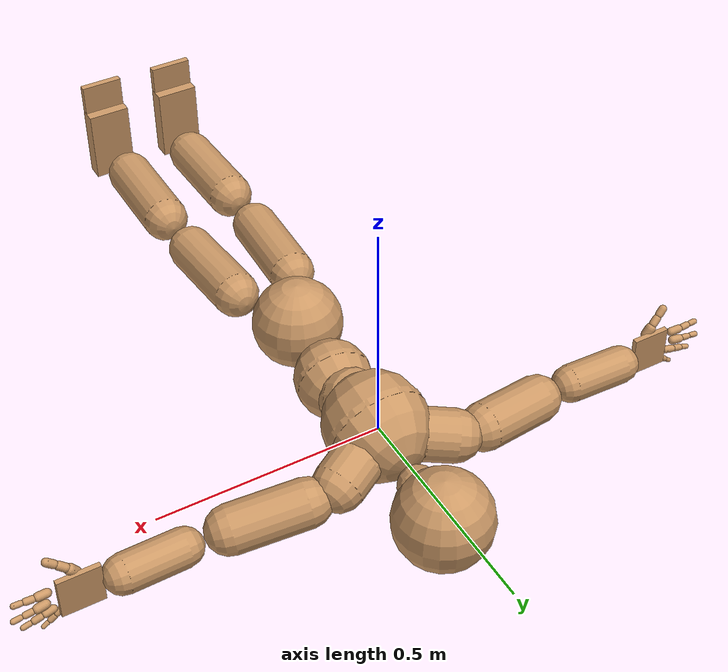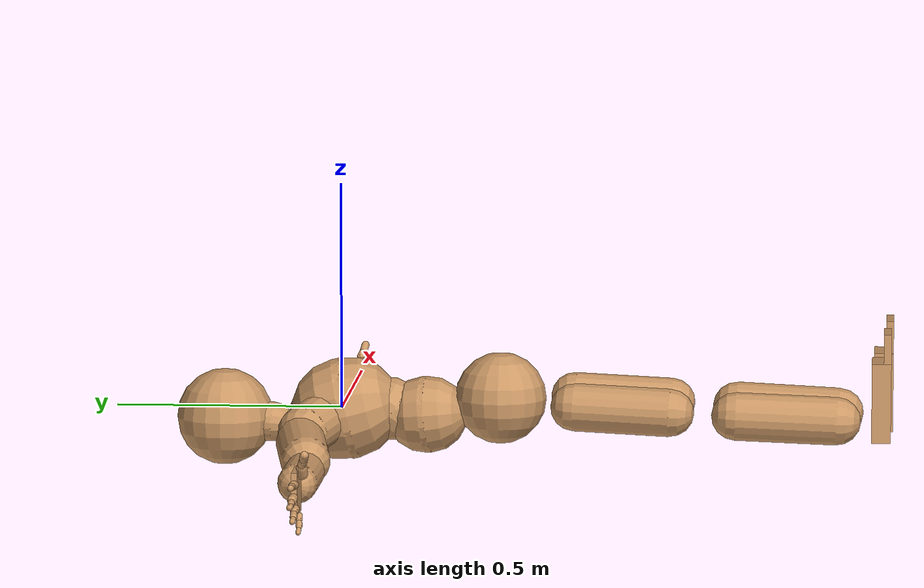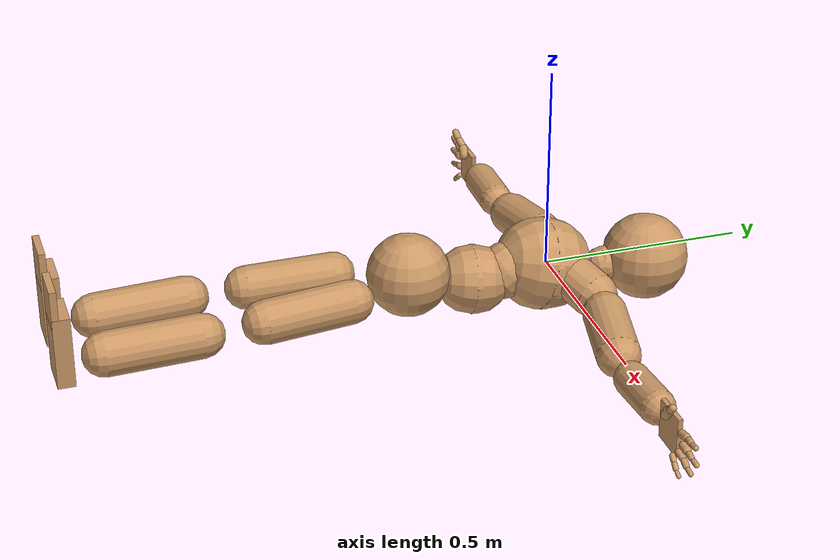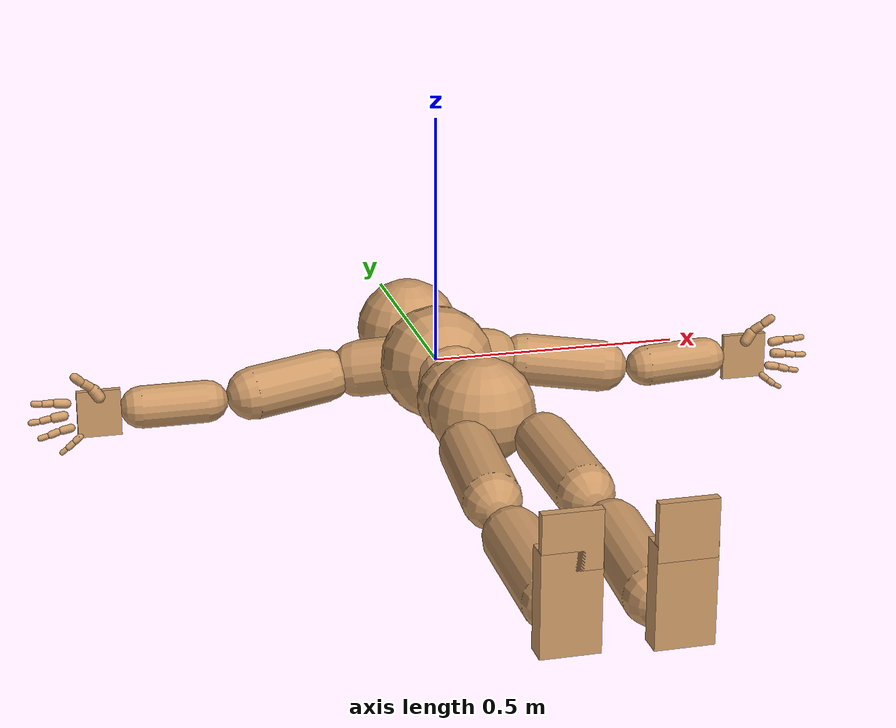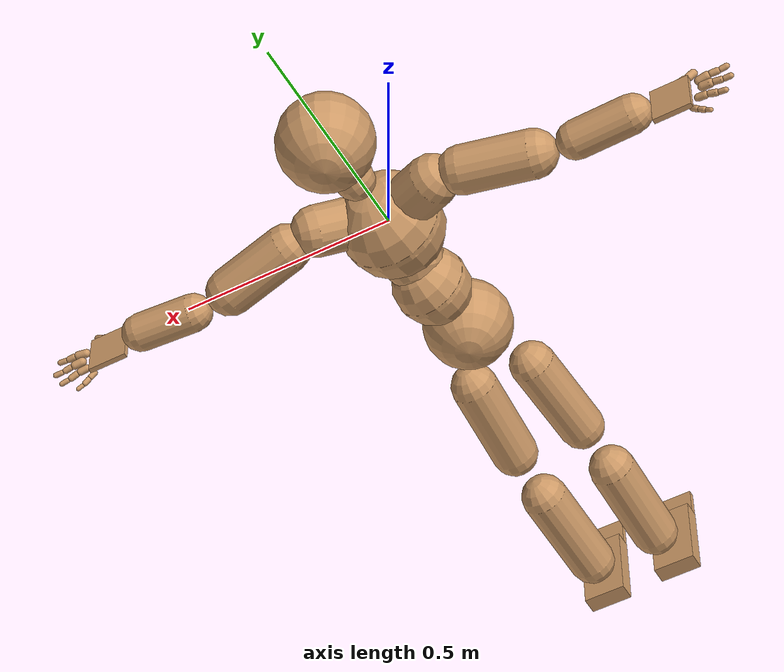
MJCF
<mujoco model="humanoid">
  <compiler coordinate="local" angle="degree"/>
  <default>
    <joint damping="0.0" armature="0.01" stiffness="0.0" limited="true"/>
    <geom conaffinity="1" condim="3" contype="7" margin="0.001" rgba="0.8 0.6 .4 1"/>
  </default>
  <asset>
    <texture type="skybox" builtin="gradient" rgb1=".4 .5 .6" rgb2="0 0 0" width="100" height="100"/>
    <texture builtin="flat" height="1278" mark="cross" markrgb="1 1 1" name="texgeom" random="0.01" rgb1="0.8 0.6 0.4" rgb2="0.8 0.6 0.4" type="cube" width="127"/>
    <texture builtin="checker" height="100" name="texplane" rgb1="0 0 0" rgb2="0.8 0.8 0.8" type="2d" width="100"/>
    <material name="MatPlane" reflectance="0.5" shininess="1" specular="1" texrepeat="60 60" texture="texplane"/>
    <material name="geom" texture="texgeom" texuniform="true"/>
  </asset>
  <worldbody>
    <body name="Pelvis" pos="0.0002 -0.3532 0.0255">
      <freejoint name="Pelvis"/>
      <geom type="sphere" contype="1" conaffinity="1" density="4629.6296296296305" size="0.1012" pos="0.0000 0.0000 0.0000" name="Pelvis"/>
      <body name="L_Hip_x_link" pos="0.0688 -0.0903 -0.0022">
        <joint name="L_Hip_x" type="hinge" pos="0 0 0" axis="1 0 0" stiffness="800" damping="80" armature="0.02" range="-90.0000 90.0000"/>
        <inertial pos="0 0 0" mass="0.0001" diaginertia="1e-9 1e-9 1e-9"/>
        <body name="L_Hip_y_link" pos="0 0 0">
          <joint name="L_Hip_y" type="hinge" pos="0 0 0" axis="0 1 0" stiffness="800" damping="80" armature="0.02" range="-90.0000 90.0000"/>
          <inertial pos="0 0 0" mass="0.0001" diaginertia="1e-9 1e-9 1e-9"/>
          <body name="L_Hip" pos="0 0 0">
            <joint name="L_Hip_z" type="hinge" pos="0 0 0" axis="0 0 1" stiffness="800" damping="80" armature="0.02" range="-90.0000 90.0000"/>
            <geom type="capsule" contype="1" conaffinity="1" density="2040.816327" fromto="0.0035 -0.0711 -0.0041 0.0142 -0.2844 -0.0162" size="0.053" name="L_Hip"/>
            <body name="L_Knee_x_link" pos="0.0177 -0.3555 -0.0203">
              <joint name="L_Knee_x" type="hinge" pos="0 0 0" axis="1 0 0" stiffness="800" damping="80" armature="0.02" range="-180.0000 180.0000"/>
              <inertial pos="0 0 0" mass="0.0001" diaginertia="1e-9 1e-9 1e-9"/>
              <body name="L_Knee_y_link" pos="0 0 0">
                <joint name="L_Knee_y" type="hinge" pos="0 0 0" axis="0 1 0" stiffness="800" damping="80" armature="0.02" range="-5.6250 5.6250"/>
                <inertial pos="0 0 0" mass="0.0001" diaginertia="1e-9 1e-9 1e-9"/>
                <body name="L_Knee" pos="0 0 0">
                  <joint name="L_Knee_z" type="hinge" pos="0 0 0" axis="0 0 1" stiffness="800" damping="80" armature="0.02" range="-5.6250 5.6250"/>
                  <geom type="capsule" contype="1" conaffinity="1" density="1234.567901" fromto="-0.0018 -0.0755 -0.0035 -0.0072 -0.3019 -0.0139" size="0.0535" name="L_Knee"/>
                  <body name="L_Ankle_x_link" pos="-0.009 -0.3774 -0.0174">
                    <joint name="L_Ankle_x" type="hinge" pos="0 0 0" axis="1 0 0" stiffness="800" damping="80" armature="0.02" range="-90.0000 90.0000"/>
                    <inertial pos="0 0 0" mass="0.0001" diaginertia="1e-9 1e-9 1e-9"/>
                    <body name="L_Ankle_y_link" pos="0 0 0">
                      <joint name="L_Ankle_y" type="hinge" pos="0 0 0" axis="0 1 0" stiffness="800" damping="80" armature="0.02" range="-90.0000 90.0000"/>
                      <inertial pos="0 0 0" mass="0.0001" diaginertia="1e-9 1e-9 1e-9"/>
                      <body name="L_Ankle" pos="0 0 0">
                        <joint name="L_Ankle_z" type="hinge" pos="0 0 0" axis="0 0 1" stiffness="800" damping="80" armature="0.02" range="-90.0000 90.0000"/>
                        <geom type="box" contype="1" conaffinity="1" density="1000.00005" pos="0.0111 -0.0220 0.0544" size="0.0497 0.0209 0.0875" quat="1.0000 0.0000 0.0000 0.0000" name="L_Ankle"/>
                        <body name="L_Toe_x_link" pos="0.0223 -0.044 0.1088">
                          <joint name="L_Toe_x" type="hinge" pos="0 0 0" axis="1 0 0" stiffness="500" damping="50" armature="0.02" range="-90.0000 90.0000"/>
                          <inertial pos="0 0 0" mass="0.0001" diaginertia="1e-9 1e-9 1e-9"/>
                          <body name="L_Toe_y_link" pos="0 0 0">
                            <joint name="L_Toe_y" type="hinge" pos="0 0 0" axis="0 1 0" stiffness="500" damping="50" armature="0.02" range="-45.0000 45.0000"/>
                            <inertial pos="0 0 0" mass="0.0001" diaginertia="1e-9 1e-9 1e-9"/>
                            <body name="L_Toe" pos="0 0 0">
                              <joint name="L_Toe_z" type="hinge" pos="0 0 0" axis="0 0 1" stiffness="500" damping="50" armature="0.02" range="-45.0000 45.0000"/>
                              <geom type="box" contype="1" conaffinity="1" density="1000.000047" pos="-0.0111 0.0091 0.0554" size="0.0491 0.0081 0.0491" quat="1.0000 0.0000 0.0000 0.0000" name="L_Toe"/>
                            </body>
                          </body>
                        </body>
                      </body>
                    </body>
                  </body>
                </body>
              </body>
            </body>
          </body>
        </body>
      </body>
      <body name="R_Hip_x_link" pos="-0.0677 -0.0965 -0.0041">
        <joint name="R_Hip_x" type="hinge" pos="0 0 0" axis="1 0 0" stiffness="800" damping="80" armature="0.02" range="-90.0000 90.0000"/>
        <inertial pos="0 0 0" mass="0.0001" diaginertia="1e-9 1e-9 1e-9"/>
        <body name="R_Hip_y_link" pos="0 0 0">
          <joint name="R_Hip_y" type="hinge" pos="0 0 0" axis="0 1 0" stiffness="800" damping="80" armature="0.02" range="-90.0000 90.0000"/>
          <inertial pos="0 0 0" mass="0.0001" diaginertia="1e-9 1e-9 1e-9"/>
          <body name="R_Hip" pos="0 0 0">
            <joint name="R_Hip_z" type="hinge" pos="0 0 0" axis="0 0 1" stiffness="800" damping="80" armature="0.02" range="-90.0000 90.0000"/>
            <geom type="capsule" contype="1" conaffinity="1" density="2040.816327" fromto="-0.0042 -0.0703 -0.0027 -0.0168 -0.2813 -0.0108" size="0.0528" name="R_Hip"/>
            <body name="R_Knee_x_link" pos="-0.0211 -0.3516 -0.0135">
              <joint name="R_Knee_x" type="hinge" pos="0 0 0" axis="1 0 0" stiffness="800" damping="80" armature="0.02" range="-180.0000 180.0000"/>
              <inertial pos="0 0 0" mass="0.0001" diaginertia="1e-9 1e-9 1e-9"/>
              <body name="R_Knee_y_link" pos="0 0 0">
                <joint name="R_Knee_y" type="hinge" pos="0 0 0" axis="0 1 0" stiffness="800" damping="80" armature="0.02" range="-5.6250 5.6250"/>
                <inertial pos="0 0 0" mass="0.0001" diaginertia="1e-9 1e-9 1e-9"/>
                <body name="R_Knee" pos="0 0 0">
                  <joint name="R_Knee_z" type="hinge" pos="0 0 0" axis="0 0 1" stiffness="800" damping="80" armature="0.02" range="-5.6250 5.6250"/>
                  <geom type="capsule" contype="1" conaffinity="1" density="1234.567901" fromto="0.0007 -0.0737 -0.0027 0.0026 -0.2949 -0.0110" size="0.0534" name="R_Knee"/>
                  <body name="R_Ankle_x_link" pos="0.0033 -0.3686 -0.0137">
                    <joint name="R_Ankle_x" type="hinge" pos="0 0 0" axis="1 0 0" stiffness="800" damping="80" armature="0.02" range="-90.0000 90.0000"/>
                    <inertial pos="0 0 0" mass="0.0001" diaginertia="1e-9 1e-9 1e-9"/>
                    <body name="R_Ankle_y_link" pos="0 0 0">
                      <joint name="R_Ankle_y" type="hinge" pos="0 0 0" axis="0 1 0" stiffness="800" damping="80" armature="0.02" range="-90.0000 90.0000"/>
                      <inertial pos="0 0 0" mass="0.0001" diaginertia="1e-9 1e-9 1e-9"/>
                      <body name="R_Ankle" pos="0 0 0">
                        <joint name="R_Ankle_z" type="hinge" pos="0 0 0" axis="0 0 1" stiffness="800" damping="80" armature="0.02" range="-90.0000 90.0000"/>
                        <geom type="box" contype="1" conaffinity="1" density="999.99999" pos="-0.0088 -0.0237 0.0513" size="0.0497 0.0209 0.0875" quat="1.0000 0.0000 0.0000 0.0000" name="R_Ankle"/>
                        <body name="R_Toe_x_link" pos="-0.0175 -0.0473 0.1027">
                          <joint name="R_Toe_x" type="hinge" pos="0 0 0" axis="1 0 0" stiffness="500" damping="50" armature="0.02" range="-90.0000 90.0000"/>
                          <inertial pos="0 0 0" mass="0.0001" diaginertia="1e-9 1e-9 1e-9"/>
                          <body name="R_Toe_y_link" pos="0 0 0">
                            <joint name="R_Toe_y" type="hinge" pos="0 0 0" axis="0 1 0" stiffness="500" damping="50" armature="0.02" range="-45.0000 45.0000"/>
                            <inertial pos="0 0 0" mass="0.0001" diaginertia="1e-9 1e-9 1e-9"/>
                            <body name="R_Toe" pos="0 0 0">
                              <joint name="R_Toe_z" type="hinge" pos="0 0 0" axis="0 0 1" stiffness="500" damping="50" armature="0.02" range="-45.0000 45.0000"/>
                              <geom type="box" contype="1" conaffinity="1" density="999.999877" pos="0.0088 0.0108 0.0523" size="0.0491 0.0081 0.0491" quat="1.0000 0.0000 0.0000 0.0000" name="R_Toe"/>
                            </body>
                          </body>
                        </body>
                      </body>
                    </body>
                  </body>
                </body>
              </body>
            </body>
          </body>
        </body>
      </body>
      <body name="Torso_x_link" pos="-0.0055 0.1042 -0.0338">
        <joint name="Torso_x" type="hinge" pos="0 0 0" axis="1 0 0" stiffness="1000" damping="100" armature="0.02" range="-60.0000 60.0000"/>
        <inertial pos="0 0 0" mass="0.0001" diaginertia="1e-9 1e-9 1e-9"/>
        <body name="Torso_y_link" pos="0 0 0">
          <joint name="Torso_y" type="hinge" pos="0 0 0" axis="0 1 0" stiffness="1000" damping="100" armature="0.02" range="-60.0000 60.0000"/>
          <inertial pos="0 0 0" mass="0.0001" diaginertia="1e-9 1e-9 1e-9"/>
          <body name="Torso" pos="0 0 0">
            <joint name="Torso_z" type="hinge" pos="0 0 0" axis="0 0 1" stiffness="1000" damping="100" armature="0.02" range="-60.0000 60.0000"/>
            <geom type="capsule" contype="1" conaffinity="1" density="2040.816327" fromto="0.0059 0.0533 -0.0050 0.0072 0.0652 -0.0061" size="0.0846" name="Torso"/>
            <body name="Spine_x_link" pos="0.0131 0.1185 -0.0112">
              <joint name="Spine_x" type="hinge" pos="0 0 0" axis="1 0 0" stiffness="1000" damping="100" armature="0.02" range="-60.0000 60.0000"/>
              <inertial pos="0 0 0" mass="0.0001" diaginertia="1e-9 1e-9 1e-9"/>
              <body name="Spine_y_link" pos="0 0 0">
                <joint name="Spine_y" type="hinge" pos="0 0 0" axis="0 1 0" stiffness="1000" damping="100" armature="0.02" range="-60.0000 60.0000"/>
                <inertial pos="0 0 0" mass="0.0001" diaginertia="1e-9 1e-9 1e-9"/>
                <body name="Spine" pos="0 0 0">
                  <joint name="Spine_z" type="hinge" pos="0 0 0" axis="0 0 1" stiffness="1000" damping="100" armature="0.02" range="-60.0000 60.0000"/>
                  <geom type="capsule" contype="1" conaffinity="1" density="2040.816327" fromto="-0.0035 0.0204 0.0159 -0.0042 0.0249 0.0195" size="0.0687" name="Spine"/>
                  <body name="Chest_x_link" pos="-0.0077 0.0453 0.0354">
                    <joint name="Chest_x" type="hinge" pos="0 0 0" axis="1 0 0" stiffness="1000" damping="100" armature="0.02" range="-60.0000 60.0000"/>
                    <inertial pos="0 0 0" mass="0.0001" diaginertia="1e-9 1e-9 1e-9"/>
                    <body name="Chest_y_link" pos="0 0 0">
                      <joint name="Chest_y" type="hinge" pos="0 0 0" axis="0 1 0" stiffness="1000" damping="100" armature="0.02" range="-60.0000 60.0000"/>
                      <inertial pos="0 0 0" mass="0.0001" diaginertia="1e-9 1e-9 1e-9"/>
                      <body name="Chest" pos="0 0 0">
                        <joint name="Chest_z" type="hinge" pos="0 0 0" axis="0 0 1" stiffness="1000" damping="100" armature="0.02" range="-60.0000 60.0000"/>
                        <geom type="capsule" contype="1" conaffinity="1" density="2040.816327" fromto="-0.0015 0.0677 -0.0157 -0.0018 0.0827 -0.0192" size="0.1139" name="Chest"/>
                        <body name="Neck_x_link" pos="-0.0065 0.2095 -0.0512">
                          <joint name="Neck_x" type="hinge" pos="0 0 0" axis="1 0 0" stiffness="500" damping="50" armature="0.02" range="-180.0000 180.0000"/>
                          <inertial pos="0 0 0" mass="0.0001" diaginertia="1e-9 1e-9 1e-9"/>
                          <body name="Neck_y_link" pos="0 0 0">
                            <joint name="Neck_y" type="hinge" pos="0 0 0" axis="0 1 0" stiffness="500" damping="50" armature="0.02" range="-180.0000 180.0000"/>
                            <inertial pos="0 0 0" mass="0.0001" diaginertia="1e-9 1e-9 1e-9"/>
                            <body name="Neck" pos="0 0 0">
                              <joint name="Neck_z" type="hinge" pos="0 0 0" axis="0 0 1" stiffness="500" damping="50" armature="0.02" range="-180.0000 180.0000"/>
                              <geom type="capsule" contype="1" conaffinity="1" density="1000" fromto="0.0019 0.0273 0.0024 0.0077 0.1090 0.0096" size="0.044" name="Neck"/>
                              <body name="Head_x_link" pos="0.0097 0.1363 0.012">
                                <joint name="Head_x" type="hinge" pos="0 0 0" axis="1 0 0" stiffness="500" damping="50" armature="0.02" range="-90.0000 90.0000"/>
                                <inertial pos="0 0 0" mass="0.0001" diaginertia="1e-9 1e-9 1e-9"/>
                                <body name="Head_y_link" pos="0 0 0">
                                  <joint name="Head_y" type="hinge" pos="0 0 0" axis="0 1 0" stiffness="500" damping="50" armature="0.02" range="-90.0000 90.0000"/>
                                  <inertial pos="0 0 0" mass="0.0001" diaginertia="1e-9 1e-9 1e-9"/>
                                  <body name="Head" pos="0 0 0">
                                    <joint name="Head_z" type="hinge" pos="0 0 0" axis="0 0 1" stiffness="500" damping="50" armature="0.02" range="-90.0000 90.0000"/>
                                    <geom type="sphere" contype="1" conaffinity="1" density="1000" size="0.1068" pos="0.0000 0.0000 0.0000" name="Head"/>
                                  </body>
                                </body>
                              </body>
                            </body>
                          </body>
                        </body>
                        <body name="L_Thorax_x_link" pos="0.0577 0.1229 -0.0233">
                          <joint name="L_Thorax_x" type="hinge" pos="0 0 0" axis="1 0 0" stiffness="500" damping="50" armature="0.02" range="-180.0000 180.0000"/>
                          <inertial pos="0 0 0" mass="0.0001" diaginertia="1e-9 1e-9 1e-9"/>
                          <body name="L_Thorax_y_link" pos="0 0 0">
                            <joint name="L_Thorax_y" type="hinge" pos="0 0 0" axis="0 1 0" stiffness="500" damping="50" armature="0.02" range="-180.0000 180.0000"/>
                            <inertial pos="0 0 0" mass="0.0001" diaginertia="1e-9 1e-9 1e-9"/>
                            <body name="L_Thorax" pos="0 0 0">
                              <joint name="L_Thorax_z" type="hinge" pos="0 0 0" axis="0 0 1" stiffness="500" damping="50" armature="0.02" range="-180.0000 180.0000"/>
                              <geom type="capsule" contype="1" conaffinity="1" density="1000" fromto="0.0191 0.0089 -0.0058 0.0764 0.0354 -0.0234" size="0.0571" name="L_Thorax"/>
                              <body name="L_Shoulder_x_link" pos="0.0955 0.0443 -0.0292">
                                <joint name="L_Shoulder_x" type="hinge" pos="0 0 0" axis="1 0 0" stiffness="500" damping="50" armature="0.02" range="-180.0000 180.0000"/>
                                <inertial pos="0 0 0" mass="0.0001" diaginertia="1e-9 1e-9 1e-9"/>
                                <body name="L_Shoulder_y_link" pos="0 0 0">
                                  <joint name="L_Shoulder_y" type="hinge" pos="0 0 0" axis="0 1 0" stiffness="500" damping="50" armature="0.02" range="-180.0000 180.0000"/>
                                  <inertial pos="0 0 0" mass="0.0001" diaginertia="1e-9 1e-9 1e-9"/>
                                  <body name="L_Shoulder" pos="0 0 0">
                                    <joint name="L_Shoulder_z" type="hinge" pos="0 0 0" axis="0 0 1" stiffness="500" damping="50" armature="0.02" range="-180.0000 180.0000"/>
                                    <geom type="capsule" contype="1" conaffinity="1" density="1000" fromto="0.0529 -0.0099 -0.0064 0.2117 -0.0395 -0.0254" size="0.0535" name="L_Shoulder"/>
                                    <body name="L_Elbow_x_link" pos="0.2647 -0.0493 -0.0318">
                                      <joint name="L_Elbow_x" type="hinge" pos="0 0 0" axis="1 0 0" stiffness="500" damping="50" armature="0.02" range="-180.0000 180.0000"/>
                                      <inertial pos="0 0 0" mass="0.0001" diaginertia="1e-9 1e-9 1e-9"/>
                                      <body name="L_Elbow_y_link" pos="0 0 0">
                                        <joint name="L_Elbow_y" type="hinge" pos="0 0 0" axis="0 1 0" stiffness="500" damping="50" armature="0.02" range="-180.0000 180.0000"/>
                                        <inertial pos="0 0 0" mass="0.0001" diaginertia="1e-9 1e-9 1e-9"/>
                                        <body name="L_Elbow" pos="0 0 0">
                                          <joint name="L_Elbow_z" type="hinge" pos="0 0 0" axis="0 0 1" stiffness="500" damping="50" armature="0.02" range="-180.0000 180.0000"/>
                                          <geom type="capsule" contype="1" conaffinity="1" density="1000" fromto="0.0435 0.0019 0.0015 0.1742 0.0077 0.0060" size="0.0423" name="L_Elbow"/>
                                          <body name="L_Wrist_x_link" pos="0.2177 0.0096 0.0075">
                                            <joint name="L_Wrist_x" type="hinge" pos="0 0 0" axis="1 0 0" stiffness="300" damping="30" armature="0.02" range="-180.0000 180.0000"/>
                                            <inertial pos="0 0 0" mass="0.0001" diaginertia="1e-9 1e-9 1e-9"/>
                                            <body name="L_Wrist_y_link" pos="0 0 0">
                                              <joint name="L_Wrist_y" type="hinge" pos="0 0 0" axis="0 1 0" stiffness="300" damping="30" armature="0.02" range="-180.0000 180.0000"/>
                                              <inertial pos="0 0 0" mass="0.0001" diaginertia="1e-9 1e-9 1e-9"/>
                                              <body name="L_Wrist" pos="0 0 0">
                                                <joint name="L_Wrist_z" type="hinge" pos="0 0 0" axis="0 0 1" stiffness="300" damping="30" armature="0.02" range="-180.0000 180.0000"/>
                                                <geom type="box" contype="1" conaffinity="1" density="2541.499718" pos="0.0416 -0.0074 -0.0022" size="0.0462 0.0059 0.0479" quat="1.0000 0.0000 0.0000 0.0000" name="L_Wrist"/>
                                                <body name="L_Index1_x_link" pos="0.0987 -0.0117 0.0223">
                                                  <joint name="L_Index1_x" type="hinge" pos="0 0 0" axis="1 0 0" stiffness="100" damping="10" armature="0.02" range="-180.0000 180.0000"/>
                                                  <inertial pos="0 0 0" mass="0.0001" diaginertia="1e-9 1e-9 1e-9"/>
                                                  <body name="L_Index1_y_link" pos="0 0 0">
                                                    <joint name="L_Index1_y" type="hinge" pos="0 0 0" axis="0 1 0" stiffness="100" damping="10" armature="0.02" range="-180.0000 180.0000"/>
                                                    <inertial pos="0 0 0" mass="0.0001" diaginertia="1e-9 1e-9 1e-9"/>
                                                    <body name="L_Index1" pos="0 0 0">
                                                      <joint name="L_Index1_z" type="hinge" pos="0 0 0" axis="0 0 1" stiffness="100" damping="10" armature="0.02" range="-180.0000 180.0000"/>
                                                      <geom type="capsule" contype="1" conaffinity="1" density="1000" fromto="0.0063 0.0007 0.0006 0.0253 0.0027 0.0023" size="0.0094" name="L_Index1"/>
                                                      <body name="L_Index2_x_link" pos="0.0316 0.0034 0.0029">
                                                        <joint name="L_Index2_x" type="hinge" pos="0 0 0" axis="1 0 0" stiffness="100" damping="10" armature="0.02" range="-180.0000 180.0000"/>
                                                        <inertial pos="0 0 0" mass="0.0001" diaginertia="1e-9 1e-9 1e-9"/>
                                                        <body name="L_Index2_y_link" pos="0 0 0">
                                                          <joint name="L_Index2_y" type="hinge" pos="0 0 0" axis="0 1 0" stiffness="100" damping="10" armature="0.02" range="-180.0000 180.0000"/>
                                                          <inertial pos="0 0 0" mass="0.0001" diaginertia="1e-9 1e-9 1e-9"/>
                                                          <body name="L_Index2" pos="0 0 0">
                                                            <joint name="L_Index2_z" type="hinge" pos="0 0 0" axis="0 0 1" stiffness="100" damping="10" armature="0.02" range="-180.0000 180.0000"/>
                                                            <geom type="capsule" contype="1" conaffinity="1" density="1000" fromto="0.0044 -0.0003 0.0001 0.0177 -0.0010 0.0003" size="0.0076" name="L_Index2"/>
                                                            <body name="L_Index3_x_link" pos="0.0221 -0.0013 0.0004">
                                                            <joint name="L_Index3_x" type="hinge" pos="0 0 0" axis="1 0 0" stiffness="100" damping="10" armature="0.02" range="-180.0000 180.0000"/>
                                                            <inertial pos="0 0 0" mass="0.0001" diaginertia="1e-9 1e-9 1e-9"/>
                                                            <body name="L_Index3_y_link" pos="0 0 0">
                                                            <joint name="L_Index3_y" type="hinge" pos="0 0 0" axis="0 1 0" stiffness="100" damping="10" armature="0.02" range="-180.0000 180.0000"/>
                                                            <inertial pos="0 0 0" mass="0.0001" diaginertia="1e-9 1e-9 1e-9"/>
                                                            <body name="L_Index3" pos="0 0 0">
                                                            <joint name="L_Index3_z" type="hinge" pos="0 0 0" axis="0 0 1" stiffness="100" damping="10" armature="0.02" range="-180.0000 180.0000"/>
                                                            <geom type="capsule" contype="1" conaffinity="1" density="1000" fromto="0.0048 0.0001 0.0005 0.0193 0.0006 0.0019" size="0.0063" name="L_Index3"/>
                                                            </body>
                                                            </body>
                                                            </body>
                                                          </body>
                                                        </body>
                                                      </body>
                                                    </body>
                                                  </body>
                                                </body>
                                                <body name="L_Middle1_x_link" pos="0.1058 -0.0092 -0.0026">
                                                  <joint name="L_Middle1_x" type="hinge" pos="0 0 0" axis="1 0 0" stiffness="100" damping="10" armature="0.02" range="-180.0000 180.0000"/>
                                                  <inertial pos="0 0 0" mass="0.0001" diaginertia="1e-9 1e-9 1e-9"/>
                                                  <body name="L_Middle1_y_link" pos="0 0 0">
                                                    <joint name="L_Middle1_y" type="hinge" pos="0 0 0" axis="0 1 0" stiffness="100" damping="10" armature="0.02" range="-180.0000 180.0000"/>
                                                    <inertial pos="0 0 0" mass="0.0001" diaginertia="1e-9 1e-9 1e-9"/>
                                                    <body name="L_Middle1" pos="0 0 0">
                                                      <joint name="L_Middle1_z" type="hinge" pos="0 0 0" axis="0 0 1" stiffness="100" damping="10" armature="0.02" range="-180.0000 180.0000"/>
                                                      <geom type="capsule" contype="1" conaffinity="1" density="1000" fromto="0.0060 0.0003 -0.0008 0.0239 0.0013 -0.0033" size="0.0098" name="L_Middle1"/>
                                                      <body name="L_Middle2_x_link" pos="0.0299 0.0016 -0.0041">
                                                        <joint name="L_Middle2_x" type="hinge" pos="0 0 0" axis="1 0 0" stiffness="100" damping="10" armature="0.02" range="-180.0000 180.0000"/>
                                                        <inertial pos="0 0 0" mass="0.0001" diaginertia="1e-9 1e-9 1e-9"/>
                                                        <body name="L_Middle2_y_link" pos="0 0 0">
                                                          <joint name="L_Middle2_y" type="hinge" pos="0 0 0" axis="0 1 0" stiffness="100" damping="10" armature="0.02" range="-180.0000 180.0000"/>
                                                          <inertial pos="0 0 0" mass="0.0001" diaginertia="1e-9 1e-9 1e-9"/>
                                                          <body name="L_Middle2" pos="0 0 0">
                                                            <joint name="L_Middle2_z" type="hinge" pos="0 0 0" axis="0 0 1" stiffness="100" damping="10" armature="0.02" range="-180.0000 180.0000"/>
                                                            <geom type="capsule" contype="1" conaffinity="1" density="1000" fromto="0.0046 -0.0002 -0.0008 0.0184 -0.0006 -0.0032" size="0.0071" name="L_Middle2"/>
                                                            <body name="L_Middle3_x_link" pos="0.023 -0.0008 -0.004">
                                                            <joint name="L_Middle3_x" type="hinge" pos="0 0 0" axis="1 0 0" stiffness="100" damping="10" armature="0.02" range="-180.0000 180.0000"/>
                                                            <inertial pos="0 0 0" mass="0.0001" diaginertia="1e-9 1e-9 1e-9"/>
                                                            <body name="L_Middle3_y_link" pos="0 0 0">
                                                            <joint name="L_Middle3_y" type="hinge" pos="0 0 0" axis="0 1 0" stiffness="100" damping="10" armature="0.02" range="-180.0000 180.0000"/>
                                                            <inertial pos="0 0 0" mass="0.0001" diaginertia="1e-9 1e-9 1e-9"/>
                                                            <body name="L_Middle3" pos="0 0 0">
                                                            <joint name="L_Middle3_z" type="hinge" pos="0 0 0" axis="0 0 1" stiffness="100" damping="10" armature="0.02" range="-180.0000 180.0000"/>
                                                            <geom type="capsule" contype="1" conaffinity="1" density="1000" fromto="0.0050 0.0002 -0.0004 0.0200 0.0010 -0.0016" size="0.0061" name="L_Middle3"/>
                                                            </body>
                                                            </body>
                                                            </body>
                                                          </body>
                                                        </body>
                                                      </body>
                                                    </body>
                                                  </body>
                                                </body>
                                                <body name="L_Pinky1_x_link" pos="0.0797 -0.0188 -0.0443">
                                                  <joint name="L_Pinky1_x" type="hinge" pos="0 0 0" axis="1 0 0" stiffness="100" damping="10" armature="0.02" range="-180.0000 180.0000"/>
                                                  <inertial pos="0 0 0" mass="0.0001" diaginertia="1e-9 1e-9 1e-9"/>
                                                  <body name="L_Pinky1_y_link" pos="0 0 0">
                                                    <joint name="L_Pinky1_y" type="hinge" pos="0 0 0" axis="0 1 0" stiffness="100" damping="10" armature="0.02" range="-180.0000 180.0000"/>
                                                    <inertial pos="0 0 0" mass="0.0001" diaginertia="1e-9 1e-9 1e-9"/>
                                                    <body name="L_Pinky1" pos="0 0 0">
                                                      <joint name="L_Pinky1_z" type="hinge" pos="0 0 0" axis="0 0 1" stiffness="100" damping="10" armature="0.02" range="-180.0000 180.0000"/>
                                                      <geom type="capsule" contype="1" conaffinity="1" density="1000" fromto="0.0029 -0.0001 -0.0025 0.0118 -0.0004 -0.0100" size="0.0069" name="L_Pinky1"/>
                                                      <body name="L_Pinky2_x_link" pos="0.0147 -0.0006 -0.0125">
                                                        <joint name="L_Pinky2_x" type="hinge" pos="0 0 0" axis="1 0 0" stiffness="100" damping="10" armature="0.02" range="-180.0000 180.0000"/>
                                                        <inertial pos="0 0 0" mass="0.0001" diaginertia="1e-9 1e-9 1e-9"/>
                                                        <body name="L_Pinky2_y_link" pos="0 0 0">
                                                          <joint name="L_Pinky2_y" type="hinge" pos="0 0 0" axis="0 1 0" stiffness="100" damping="10" armature="0.02" range="-180.0000 180.0000"/>
                                                          <inertial pos="0 0 0" mass="0.0001" diaginertia="1e-9 1e-9 1e-9"/>
                                                          <body name="L_Pinky2" pos="0 0 0">
                                                            <joint name="L_Pinky2_z" type="hinge" pos="0 0 0" axis="0 0 1" stiffness="100" damping="10" armature="0.02" range="-180.0000 180.0000"/>
                                                            <geom type="capsule" contype="1" conaffinity="1" density="1000" fromto="0.0030 -0.0002 -0.0023 0.0118 -0.0008 -0.0093" size="0.0066" name="L_Pinky2"/>
                                                            <body name="L_Pinky3_x_link" pos="0.0148 -0.001 -0.0117">
                                                            <joint name="L_Pinky3_x" type="hinge" pos="0 0 0" axis="1 0 0" stiffness="100" damping="10" armature="0.02" range="-180.0000 180.0000"/>
                                                            <inertial pos="0 0 0" mass="0.0001" diaginertia="1e-9 1e-9 1e-9"/>
                                                            <body name="L_Pinky3_y_link" pos="0 0 0">
                                                            <joint name="L_Pinky3_y" type="hinge" pos="0 0 0" axis="0 1 0" stiffness="100" damping="10" armature="0.02" range="-180.0000 180.0000"/>
                                                            <inertial pos="0 0 0" mass="0.0001" diaginertia="1e-9 1e-9 1e-9"/>
                                                            <body name="L_Pinky3" pos="0 0 0">
                                                            <joint name="L_Pinky3_z" type="hinge" pos="0 0 0" axis="0 0 1" stiffness="100" damping="10" armature="0.02" range="-180.0000 180.0000"/>
                                                            <geom type="capsule" contype="1" conaffinity="1" density="1000" fromto="0.0034 0.0002 -0.0019 0.0134 0.0008 -0.0077" size="0.0049" name="L_Pinky3"/>
                                                            </body>
                                                            </body>
                                                            </body>
                                                          </body>
                                                        </body>
                                                      </body>
                                                    </body>
                                                  </body>
                                                </body>
                                                <body name="L_Ring1_x_link" pos="0.0933 -0.0127 -0.0276">
                                                  <joint name="L_Ring1_x" type="hinge" pos="0 0 0" axis="1 0 0" stiffness="100" damping="10" armature="0.02" range="-180.0000 180.0000"/>
                                                  <inertial pos="0 0 0" mass="0.0001" diaginertia="1e-9 1e-9 1e-9"/>
                                                  <body name="L_Ring1_y_link" pos="0 0 0">
                                                    <joint name="L_Ring1_y" type="hinge" pos="0 0 0" axis="0 1 0" stiffness="100" damping="10" armature="0.02" range="-180.0000 180.0000"/>
                                                    <inertial pos="0 0 0" mass="0.0001" diaginertia="1e-9 1e-9 1e-9"/>
                                                    <body name="L_Ring1" pos="0 0 0">
                                                      <joint name="L_Ring1_z" type="hinge" pos="0 0 0" axis="0 0 1" stiffness="100" damping="10" armature="0.02" range="-180.0000 180.0000"/>
                                                      <geom type="capsule" contype="1" conaffinity="1" density="1000" fromto="0.0055 0.0004 -0.0012 0.0220 0.0015 -0.0047" size="0.0084" name="L_Ring1"/>
                                                      <body name="L_Ring2_x_link" pos="0.0275 0.0019 -0.0059">
                                                        <joint name="L_Ring2_x" type="hinge" pos="0 0 0" axis="1 0 0" stiffness="100" damping="10" armature="0.02" range="-180.0000 180.0000"/>
                                                        <inertial pos="0 0 0" mass="0.0001" diaginertia="1e-9 1e-9 1e-9"/>
                                                        <body name="L_Ring2_y_link" pos="0 0 0">
                                                          <joint name="L_Ring2_y" type="hinge" pos="0 0 0" axis="0 1 0" stiffness="100" damping="10" armature="0.02" range="-180.0000 180.0000"/>
                                                          <inertial pos="0 0 0" mass="0.0001" diaginertia="1e-9 1e-9 1e-9"/>
                                                          <body name="L_Ring2" pos="0 0 0">
                                                            <joint name="L_Ring2_z" type="hinge" pos="0 0 0" axis="0 0 1" stiffness="100" damping="10" armature="0.02" range="-180.0000 180.0000"/>
                                                            <geom type="capsule" contype="1" conaffinity="1" density="1000" fromto="0.0044 -0.0002 -0.0015 0.0178 -0.0010 -0.0060" size="0.0076" name="L_Ring2"/>
                                                            <body name="L_Ring3_x_link" pos="0.0222 -0.0012 -0.0074">
                                                            <joint name="L_Ring3_x" type="hinge" pos="0 0 0" axis="1 0 0" stiffness="100" damping="10" armature="0.02" range="-180.0000 180.0000"/>
                                                            <inertial pos="0 0 0" mass="0.0001" diaginertia="1e-9 1e-9 1e-9"/>
                                                            <body name="L_Ring3_y_link" pos="0 0 0">
                                                            <joint name="L_Ring3_y" type="hinge" pos="0 0 0" axis="0 1 0" stiffness="100" damping="10" armature="0.02" range="-180.0000 180.0000"/>
                                                            <inertial pos="0 0 0" mass="0.0001" diaginertia="1e-9 1e-9 1e-9"/>
                                                            <body name="L_Ring3" pos="0 0 0">
                                                            <joint name="L_Ring3_z" type="hinge" pos="0 0 0" axis="0 0 1" stiffness="100" damping="10" armature="0.02" range="-180.0000 180.0000"/>
                                                            <geom type="capsule" contype="1" conaffinity="1" density="1000" fromto="0.0048 0.0002 -0.0011 0.0194 0.0006 -0.0044" size="0.0058" name="L_Ring3"/>
                                                            </body>
                                                            </body>
                                                            </body>
                                                          </body>
                                                        </body>
                                                      </body>
                                                    </body>
                                                  </body>
                                                </body>
                                                <body name="L_Thumb1_x_link" pos="0.0385 -0.0215 0.0297">
                                                  <joint name="L_Thumb1_x" type="hinge" pos="0 0 0" axis="1 0 0" stiffness="100" damping="10" armature="0.02" range="-180.0000 180.0000"/>
                                                  <inertial pos="0 0 0" mass="0.0001" diaginertia="1e-9 1e-9 1e-9"/>
                                                  <body name="L_Thumb1_y_link" pos="0 0 0">
                                                    <joint name="L_Thumb1_y" type="hinge" pos="0 0 0" axis="0 1 0" stiffness="100" damping="10" armature="0.02" range="-180.0000 180.0000"/>
                                                    <inertial pos="0 0 0" mass="0.0001" diaginertia="1e-9 1e-9 1e-9"/>
                                                    <body name="L_Thumb1" pos="0 0 0">
                                                      <joint name="L_Thumb1_z" type="hinge" pos="0 0 0" axis="0 0 1" stiffness="100" damping="10" armature="0.02" range="-180.0000 180.0000"/>
                                                      <geom type="capsule" contype="1" conaffinity="1" density="1000" fromto="0.0032 0.0002 0.0050 0.0129 0.0008 0.0200" size="0.012" name="L_Thumb1"/>
                                                      <body name="L_Thumb2_x_link" pos="0.0162 0.001 0.025">
                                                        <joint name="L_Thumb2_x" type="hinge" pos="0 0 0" axis="1 0 0" stiffness="100" damping="10" armature="0.02" range="-180.0000 180.0000"/>
                                                        <inertial pos="0 0 0" mass="0.0001" diaginertia="1e-9 1e-9 1e-9"/>
                                                        <body name="L_Thumb2_y_link" pos="0 0 0">
                                                          <joint name="L_Thumb2_y" type="hinge" pos="0 0 0" axis="0 1 0" stiffness="100" damping="10" armature="0.02" range="-180.0000 180.0000"/>
                                                          <inertial pos="0 0 0" mass="0.0001" diaginertia="1e-9 1e-9 1e-9"/>
                                                          <body name="L_Thumb2" pos="0 0 0">
                                                            <joint name="L_Thumb2_z" type="hinge" pos="0 0 0" axis="0 0 1" stiffness="100" damping="10" armature="0.02" range="-180.0000 180.0000"/>
                                                            <geom type="capsule" contype="1" conaffinity="1" density="1000" fromto="0.0039 -0.0013 0.0030 0.0156 -0.0050 0.0119" size="0.0094" name="L_Thumb2"/>
                                                            <body name="L_Thumb3_x_link" pos="0.0194 -0.0063 0.0149">
                                                            <joint name="L_Thumb3_x" type="hinge" pos="0 0 0" axis="1 0 0" stiffness="100" damping="10" armature="0.02" range="-180.0000 180.0000"/>
                                                            <inertial pos="0 0 0" mass="0.0001" diaginertia="1e-9 1e-9 1e-9"/>
                                                            <body name="L_Thumb3_y_link" pos="0 0 0">
                                                            <joint name="L_Thumb3_y" type="hinge" pos="0 0 0" axis="0 1 0" stiffness="100" damping="10" armature="0.02" range="-180.0000 180.0000"/>
                                                            <inertial pos="0 0 0" mass="0.0001" diaginertia="1e-9 1e-9 1e-9"/>
                                                            <body name="L_Thumb3" pos="0 0 0">
                                                            <joint name="L_Thumb3_z" type="hinge" pos="0 0 0" axis="0 0 1" stiffness="100" damping="10" armature="0.02" range="-180.0000 180.0000"/>
                                                            <geom type="capsule" contype="1" conaffinity="1" density="1000" fromto="0.0043 -0.0009 0.0034 0.0172 -0.0034 0.0135" size="0.009" name="L_Thumb3"/>
                                                            </body>
                                                            </body>
                                                            </body>
                                                          </body>
                                                        </body>
                                                      </body>
                                                    </body>
                                                  </body>
                                                </body>
                                              </body>
                                            </body>
                                          </body>
                                        </body>
                                      </body>
                                    </body>
                                  </body>
                                </body>
                              </body>
                            </body>
                          </body>
                        </body>
                        <body name="R_Thorax_x_link" pos="-0.061 0.1187 -0.0303">
                          <joint name="R_Thorax_x" type="hinge" pos="0 0 0" axis="1 0 0" stiffness="500" damping="50" armature="0.02" range="-180.0000 180.0000"/>
                          <inertial pos="0 0 0" mass="0.0001" diaginertia="1e-9 1e-9 1e-9"/>
                          <body name="R_Thorax_y_link" pos="0 0 0">
                            <joint name="R_Thorax_y" type="hinge" pos="0 0 0" axis="0 1 0" stiffness="500" damping="50" armature="0.02" range="-180.0000 180.0000"/>
                            <inertial pos="0 0 0" mass="0.0001" diaginertia="1e-9 1e-9 1e-9"/>
                            <body name="R_Thorax" pos="0 0 0">
                              <joint name="R_Thorax_z" type="hinge" pos="0 0 0" axis="0 0 1" stiffness="500" damping="50" armature="0.02" range="-180.0000 180.0000"/>
                              <geom type="capsule" contype="1" conaffinity="1" density="1000" fromto="-0.0207 0.0092 -0.0043 -0.0826 0.0368 -0.0172" size="0.0583" name="R_Thorax"/>
                              <body name="R_Shoulder_x_link" pos="-0.1033 0.046 -0.0215">
                                <joint name="R_Shoulder_x" type="hinge" pos="0 0 0" axis="1 0 0" stiffness="500" damping="50" armature="0.02" range="-180.0000 180.0000"/>
                                <inertial pos="0 0 0" mass="0.0001" diaginertia="1e-9 1e-9 1e-9"/>
                                <body name="R_Shoulder_y_link" pos="0 0 0">
                                  <joint name="R_Shoulder_y" type="hinge" pos="0 0 0" axis="0 1 0" stiffness="500" damping="50" armature="0.02" range="-180.0000 180.0000"/>
                                  <inertial pos="0 0 0" mass="0.0001" diaginertia="1e-9 1e-9 1e-9"/>
                                  <body name="R_Shoulder" pos="0 0 0">
                                    <joint name="R_Shoulder_z" type="hinge" pos="0 0 0" axis="0 0 1" stiffness="500" damping="50" armature="0.02" range="-180.0000 180.0000"/>
                                    <geom type="capsule" contype="1" conaffinity="1" density="1000" fromto="-0.0509 -0.0087 -0.0049 -0.2037 -0.0346 -0.0197" size="0.054" name="R_Shoulder"/>
                                    <body name="R_Elbow_x_link" pos="-0.2546 -0.0433 -0.0246">
                                      <joint name="R_Elbow_x" type="hinge" pos="0 0 0" axis="1 0 0" stiffness="500" damping="50" armature="0.02" range="-180.0000 180.0000"/>
                                      <inertial pos="0 0 0" mass="0.0001" diaginertia="1e-9 1e-9 1e-9"/>
                                      <body name="R_Elbow_y_link" pos="0 0 0">
                                        <joint name="R_Elbow_y" type="hinge" pos="0 0 0" axis="0 1 0" stiffness="500" damping="50" armature="0.02" range="-180.0000 180.0000"/>
                                        <inertial pos="0 0 0" mass="0.0001" diaginertia="1e-9 1e-9 1e-9"/>
                                        <body name="R_Elbow" pos="0 0 0">
                                          <joint name="R_Elbow_z" type="hinge" pos="0 0 0" axis="0 0 1" stiffness="500" damping="50" armature="0.02" range="-180.0000 180.0000"/>
                                          <geom type="capsule" contype="1" conaffinity="1" density="1000" fromto="-0.0436 0.0010 -0.0004 -0.1744 0.0041 -0.0017" size="0.0425" name="R_Elbow"/>
                                          <body name="R_Wrist_x_link" pos="-0.218 0.0052 -0.0021">
                                            <joint name="R_Wrist_x" type="hinge" pos="0 0 0" axis="1 0 0" stiffness="300" damping="30" armature="0.02" range="-180.0000 180.0000"/>
                                            <inertial pos="0 0 0" mass="0.0001" diaginertia="1e-9 1e-9 1e-9"/>
                                            <body name="R_Wrist_y_link" pos="0 0 0">
                                              <joint name="R_Wrist_y" type="hinge" pos="0 0 0" axis="0 1 0" stiffness="300" damping="30" armature="0.02" range="-180.0000 180.0000"/>
                                              <inertial pos="0 0 0" mass="0.0001" diaginertia="1e-9 1e-9 1e-9"/>
                                              <body name="R_Wrist" pos="0 0 0">
                                                <joint name="R_Wrist_z" type="hinge" pos="0 0 0" axis="0 0 1" stiffness="300" damping="30" armature="0.02" range="-180.0000 180.0000"/>
                                                <geom type="box" contype="1" conaffinity="1" density="2541.50015" pos="-0.0411 -0.0069 -0.0014" size="0.0433 0.0061 0.0479" quat="1.0000 0.0000 0.0000 0.0000" name="R_Wrist"/>
                                                <body name="R_Index1_x_link" pos="-0.0976 -0.0108 0.0241">
                                                  <joint name="R_Index1_x" type="hinge" pos="0 0 0" axis="1 0 0" stiffness="100" damping="10" armature="0.02" range="-180.0000 180.0000"/>
                                                  <inertial pos="0 0 0" mass="0.0001" diaginertia="1e-9 1e-9 1e-9"/>
                                                  <body name="R_Index1_y_link" pos="0 0 0">
                                                    <joint name="R_Index1_y" type="hinge" pos="0 0 0" axis="0 1 0" stiffness="100" damping="10" armature="0.02" range="-180.0000 180.0000"/>
                                                    <inertial pos="0 0 0" mass="0.0001" diaginertia="1e-9 1e-9 1e-9"/>
                                                    <body name="R_Index1" pos="0 0 0">
                                                      <joint name="R_Index1_z" type="hinge" pos="0 0 0" axis="0 0 1" stiffness="100" damping="10" armature="0.02" range="-180.0000 180.0000"/>
                                                      <geom type="capsule" contype="1" conaffinity="1" density="1000" fromto="-0.0063 0.0007 0.0006 -0.0253 0.0027 0.0023" size="0.0094" name="R_Index1"/>
                                                      <body name="R_Index2_x_link" pos="-0.0316 0.0034 0.0029">
                                                        <joint name="R_Index2_x" type="hinge" pos="0 0 0" axis="1 0 0" stiffness="100" damping="10" armature="0.02" range="-180.0000 180.0000"/>
                                                        <inertial pos="0 0 0" mass="0.0001" diaginertia="1e-9 1e-9 1e-9"/>
                                                        <body name="R_Index2_y_link" pos="0 0 0">
                                                          <joint name="R_Index2_y" type="hinge" pos="0 0 0" axis="0 1 0" stiffness="100" damping="10" armature="0.02" range="-180.0000 180.0000"/>
                                                          <inertial pos="0 0 0" mass="0.0001" diaginertia="1e-9 1e-9 1e-9"/>
                                                          <body name="R_Index2" pos="0 0 0">
                                                            <joint name="R_Index2_z" type="hinge" pos="0 0 0" axis="0 0 1" stiffness="100" damping="10" armature="0.02" range="-180.0000 180.0000"/>
                                                            <geom type="capsule" contype="1" conaffinity="1" density="1000" fromto="-0.0044 -0.0003 0.0001 -0.0177 -0.0010 0.0003" size="0.0076" name="R_Index2"/>
                                                            <body name="R_Index3_x_link" pos="-0.0221 -0.0013 0.0004">
                                                            <joint name="R_Index3_x" type="hinge" pos="0 0 0" axis="1 0 0" stiffness="100" damping="10" armature="0.02" range="-180.0000 180.0000"/>
                                                            <inertial pos="0 0 0" mass="0.0001" diaginertia="1e-9 1e-9 1e-9"/>
                                                            <body name="R_Index3_y_link" pos="0 0 0">
                                                            <joint name="R_Index3_y" type="hinge" pos="0 0 0" axis="0 1 0" stiffness="100" damping="10" armature="0.02" range="-180.0000 180.0000"/>
                                                            <inertial pos="0 0 0" mass="0.0001" diaginertia="1e-9 1e-9 1e-9"/>
                                                            <body name="R_Index3" pos="0 0 0">
                                                            <joint name="R_Index3_z" type="hinge" pos="0 0 0" axis="0 0 1" stiffness="100" damping="10" armature="0.02" range="-180.0000 180.0000"/>
                                                            <geom type="capsule" contype="1" conaffinity="1" density="1000" fromto="-0.0040 0.0001 0.0005 -0.0161 0.0006 0.0019" size="0.0066" name="R_Index3"/>
                                                            </body>
                                                            </body>
                                                            </body>
                                                          </body>
                                                        </body>
                                                      </body>
                                                    </body>
                                                  </body>
                                                </body>
                                                <body name="R_Middle1_x_link" pos="-0.1046 -0.0083 -0.0008">
                                                  <joint name="R_Middle1_x" type="hinge" pos="0 0 0" axis="1 0 0" stiffness="100" damping="10" armature="0.02" range="-180.0000 180.0000"/>
                                                  <inertial pos="0 0 0" mass="0.0001" diaginertia="1e-9 1e-9 1e-9"/>
                                                  <body name="R_Middle1_y_link" pos="0 0 0">
                                                    <joint name="R_Middle1_y" type="hinge" pos="0 0 0" axis="0 1 0" stiffness="100" damping="10" armature="0.02" range="-180.0000 180.0000"/>
                                                    <inertial pos="0 0 0" mass="0.0001" diaginertia="1e-9 1e-9 1e-9"/>
                                                    <body name="R_Middle1" pos="0 0 0">
                                                      <joint name="R_Middle1_z" type="hinge" pos="0 0 0" axis="0 0 1" stiffness="100" damping="10" armature="0.02" range="-180.0000 180.0000"/>
                                                      <geom type="capsule" contype="1" conaffinity="1" density="1000" fromto="-0.0060 0.0003 -0.0008 -0.0239 0.0013 -0.0033" size="0.0098" name="R_Middle1"/>
                                                      <body name="R_Middle2_x_link" pos="-0.0299 0.0016 -0.0041">
                                                        <joint name="R_Middle2_x" type="hinge" pos="0 0 0" axis="1 0 0" stiffness="100" damping="10" armature="0.02" range="-180.0000 180.0000"/>
                                                        <inertial pos="0 0 0" mass="0.0001" diaginertia="1e-9 1e-9 1e-9"/>
                                                        <body name="R_Middle2_y_link" pos="0 0 0">
                                                          <joint name="R_Middle2_y" type="hinge" pos="0 0 0" axis="0 1 0" stiffness="100" damping="10" armature="0.02" range="-180.0000 180.0000"/>
                                                          <inertial pos="0 0 0" mass="0.0001" diaginertia="1e-9 1e-9 1e-9"/>
                                                          <body name="R_Middle2" pos="0 0 0">
                                                            <joint name="R_Middle2_z" type="hinge" pos="0 0 0" axis="0 0 1" stiffness="100" damping="10" armature="0.02" range="-180.0000 180.0000"/>
                                                            <geom type="capsule" contype="1" conaffinity="1" density="1000" fromto="-0.0046 -0.0002 -0.0008 -0.0184 -0.0006 -0.0032" size="0.0071" name="R_Middle2"/>
                                                            <body name="R_Middle3_x_link" pos="-0.023 -0.0008 -0.004">
                                                            <joint name="R_Middle3_x" type="hinge" pos="0 0 0" axis="1 0 0" stiffness="100" damping="10" armature="0.02" range="-180.0000 180.0000"/>
                                                            <inertial pos="0 0 0" mass="0.0001" diaginertia="1e-9 1e-9 1e-9"/>
                                                            <body name="R_Middle3_y_link" pos="0 0 0">
                                                            <joint name="R_Middle3_y" type="hinge" pos="0 0 0" axis="0 1 0" stiffness="100" damping="10" armature="0.02" range="-180.0000 180.0000"/>
                                                            <inertial pos="0 0 0" mass="0.0001" diaginertia="1e-9 1e-9 1e-9"/>
                                                            <body name="R_Middle3" pos="0 0 0">
                                                            <joint name="R_Middle3_z" type="hinge" pos="0 0 0" axis="0 0 1" stiffness="100" damping="10" armature="0.02" range="-180.0000 180.0000"/>
                                                            <geom type="capsule" contype="1" conaffinity="1" density="1000" fromto="-0.0042 0.0002 -0.0004 -0.0168 0.0010 -0.0016" size="0.0064" name="R_Middle3"/>
                                                            </body>
                                                            </body>
                                                            </body>
                                                          </body>
                                                        </body>
                                                      </body>
                                                    </body>
                                                  </body>
                                                </body>
                                                <body name="R_Pinky1_x_link" pos="-0.0786 -0.0179 -0.0425">
                                                  <joint name="R_Pinky1_x" type="hinge" pos="0 0 0" axis="1 0 0" stiffness="100" damping="10" armature="0.02" range="-180.0000 180.0000"/>
                                                  <inertial pos="0 0 0" mass="0.0001" diaginertia="1e-9 1e-9 1e-9"/>
                                                  <body name="R_Pinky1_y_link" pos="0 0 0">
                                                    <joint name="R_Pinky1_y" type="hinge" pos="0 0 0" axis="0 1 0" stiffness="100" damping="10" armature="0.02" range="-180.0000 180.0000"/>
                                                    <inertial pos="0 0 0" mass="0.0001" diaginertia="1e-9 1e-9 1e-9"/>
                                                    <body name="R_Pinky1" pos="0 0 0">
                                                      <joint name="R_Pinky1_z" type="hinge" pos="0 0 0" axis="0 0 1" stiffness="100" damping="10" armature="0.02" range="-180.0000 180.0000"/>
                                                      <geom type="capsule" contype="1" conaffinity="1" density="1000" fromto="-0.0029 -0.0001 -0.0025 -0.0118 -0.0004 -0.0100" size="0.0069" name="R_Pinky1"/>
                                                      <body name="R_Pinky2_x_link" pos="-0.0147 -0.0006 -0.0125">
                                                        <joint name="R_Pinky2_x" type="hinge" pos="0 0 0" axis="1 0 0" stiffness="100" damping="10" armature="0.02" range="-180.0000 180.0000"/>
                                                        <inertial pos="0 0 0" mass="0.0001" diaginertia="1e-9 1e-9 1e-9"/>
                                                        <body name="R_Pinky2_y_link" pos="0 0 0">
                                                          <joint name="R_Pinky2_y" type="hinge" pos="0 0 0" axis="0 1 0" stiffness="100" damping="10" armature="0.02" range="-180.0000 180.0000"/>
                                                          <inertial pos="0 0 0" mass="0.0001" diaginertia="1e-9 1e-9 1e-9"/>
                                                          <body name="R_Pinky2" pos="0 0 0">
                                                            <joint name="R_Pinky2_z" type="hinge" pos="0 0 0" axis="0 0 1" stiffness="100" damping="10" armature="0.02" range="-180.0000 180.0000"/>
                                                            <geom type="capsule" contype="1" conaffinity="1" density="1000" fromto="-0.0030 -0.0002 -0.0023 -0.0118 -0.0008 -0.0093" size="0.0066" name="R_Pinky2"/>
                                                            <body name="R_Pinky3_x_link" pos="-0.0148 -0.001 -0.0117">
                                                            <joint name="R_Pinky3_x" type="hinge" pos="0 0 0" axis="1 0 0" stiffness="100" damping="10" armature="0.02" range="-180.0000 180.0000"/>
                                                            <inertial pos="0 0 0" mass="0.0001" diaginertia="1e-9 1e-9 1e-9"/>
                                                            <body name="R_Pinky3_y_link" pos="0 0 0">
                                                            <joint name="R_Pinky3_y" type="hinge" pos="0 0 0" axis="0 1 0" stiffness="100" damping="10" armature="0.02" range="-180.0000 180.0000"/>
                                                            <inertial pos="0 0 0" mass="0.0001" diaginertia="1e-9 1e-9 1e-9"/>
                                                            <body name="R_Pinky3" pos="0 0 0">
                                                            <joint name="R_Pinky3_z" type="hinge" pos="0 0 0" axis="0 0 1" stiffness="100" damping="10" armature="0.02" range="-180.0000 180.0000"/>
                                                            <geom type="capsule" contype="1" conaffinity="1" density="1000" fromto="-0.0026 0.0002 -0.0019 -0.0102 0.0008 -0.0077" size="0.0052" name="R_Pinky3"/>
                                                            </body>
                                                            </body>
                                                            </body>
                                                          </body>
                                                        </body>
                                                      </body>
                                                    </body>
                                                  </body>
                                                </body>
                                                <body name="R_Ring1_x_link" pos="-0.0922 -0.0118 -0.0259">
                                                  <joint name="R_Ring1_x" type="hinge" pos="0 0 0" axis="1 0 0" stiffness="100" damping="10" armature="0.02" range="-180.0000 180.0000"/>
                                                  <inertial pos="0 0 0" mass="0.0001" diaginertia="1e-9 1e-9 1e-9"/>
                                                  <body name="R_Ring1_y_link" pos="0 0 0">
                                                    <joint name="R_Ring1_y" type="hinge" pos="0 0 0" axis="0 1 0" stiffness="100" damping="10" armature="0.02" range="-180.0000 180.0000"/>
                                                    <inertial pos="0 0 0" mass="0.0001" diaginertia="1e-9 1e-9 1e-9"/>
                                                    <body name="R_Ring1" pos="0 0 0">
                                                      <joint name="R_Ring1_z" type="hinge" pos="0 0 0" axis="0 0 1" stiffness="100" damping="10" armature="0.02" range="-180.0000 180.0000"/>
                                                      <geom type="capsule" contype="1" conaffinity="1" density="1000" fromto="-0.0055 0.0004 -0.0012 -0.0220 0.0015 -0.0047" size="0.0084" name="R_Ring1"/>
                                                      <body name="R_Ring2_x_link" pos="-0.0275 0.0019 -0.0059">
                                                        <joint name="R_Ring2_x" type="hinge" pos="0 0 0" axis="1 0 0" stiffness="100" damping="10" armature="0.02" range="-180.0000 180.0000"/>
                                                        <inertial pos="0 0 0" mass="0.0001" diaginertia="1e-9 1e-9 1e-9"/>
                                                        <body name="R_Ring2_y_link" pos="0 0 0">
                                                          <joint name="R_Ring2_y" type="hinge" pos="0 0 0" axis="0 1 0" stiffness="100" damping="10" armature="0.02" range="-180.0000 180.0000"/>
                                                          <inertial pos="0 0 0" mass="0.0001" diaginertia="1e-9 1e-9 1e-9"/>
                                                          <body name="R_Ring2" pos="0 0 0">
                                                            <joint name="R_Ring2_z" type="hinge" pos="0 0 0" axis="0 0 1" stiffness="100" damping="10" armature="0.02" range="-180.0000 180.0000"/>
                                                            <geom type="capsule" contype="1" conaffinity="1" density="1000" fromto="-0.0044 -0.0002 -0.0015 -0.0178 -0.0010 -0.0060" size="0.0076" name="R_Ring2"/>
                                                            <body name="R_Ring3_x_link" pos="-0.0222 -0.0012 -0.0074">
                                                            <joint name="R_Ring3_x" type="hinge" pos="0 0 0" axis="1 0 0" stiffness="100" damping="10" armature="0.02" range="-180.0000 180.0000"/>
                                                            <inertial pos="0 0 0" mass="0.0001" diaginertia="1e-9 1e-9 1e-9"/>
                                                            <body name="R_Ring3_y_link" pos="0 0 0">
                                                            <joint name="R_Ring3_y" type="hinge" pos="0 0 0" axis="0 1 0" stiffness="100" damping="10" armature="0.02" range="-180.0000 180.0000"/>
                                                            <inertial pos="0 0 0" mass="0.0001" diaginertia="1e-9 1e-9 1e-9"/>
                                                            <body name="R_Ring3" pos="0 0 0">
                                                            <joint name="R_Ring3_z" type="hinge" pos="0 0 0" axis="0 0 1" stiffness="100" damping="10" armature="0.02" range="-180.0000 180.0000"/>
                                                            <geom type="capsule" contype="1" conaffinity="1" density="1000" fromto="-0.0040 0.0002 -0.0011 -0.0162 0.0006 -0.0044" size="0.0061" name="R_Ring3"/>
                                                            </body>
                                                            </body>
                                                            </body>
                                                          </body>
                                                        </body>
                                                      </body>
                                                    </body>
                                                  </body>
                                                </body>
                                                <body name="R_Thumb1_x_link" pos="-0.0374 -0.0206 0.0315">
                                                  <joint name="R_Thumb1_x" type="hinge" pos="0 0 0" axis="1 0 0" stiffness="100" damping="10" armature="0.02" range="-180.0000 180.0000"/>
                                                  <inertial pos="0 0 0" mass="0.0001" diaginertia="1e-9 1e-9 1e-9"/>
                                                  <body name="R_Thumb1_y_link" pos="0 0 0">
                                                    <joint name="R_Thumb1_y" type="hinge" pos="0 0 0" axis="0 1 0" stiffness="100" damping="10" armature="0.02" range="-180.0000 180.0000"/>
                                                    <inertial pos="0 0 0" mass="0.0001" diaginertia="1e-9 1e-9 1e-9"/>
                                                    <body name="R_Thumb1" pos="0 0 0">
                                                      <joint name="R_Thumb1_z" type="hinge" pos="0 0 0" axis="0 0 1" stiffness="100" damping="10" armature="0.02" range="-180.0000 180.0000"/>
                                                      <geom type="capsule" contype="1" conaffinity="1" density="1000" fromto="-0.0032 0.0002 0.0050 -0.0129 0.0008 0.0200" size="0.012" name="R_Thumb1"/>
                                                      <body name="R_Thumb2_x_link" pos="-0.0162 0.001 0.025">
                                                        <joint name="R_Thumb2_x" type="hinge" pos="0 0 0" axis="1 0 0" stiffness="100" damping="10" armature="0.02" range="-180.0000 180.0000"/>
                                                        <inertial pos="0 0 0" mass="0.0001" diaginertia="1e-9 1e-9 1e-9"/>
                                                        <body name="R_Thumb2_y_link" pos="0 0 0">
                                                          <joint name="R_Thumb2_y" type="hinge" pos="0 0 0" axis="0 1 0" stiffness="100" damping="10" armature="0.02" range="-180.0000 180.0000"/>
                                                          <inertial pos="0 0 0" mass="0.0001" diaginertia="1e-9 1e-9 1e-9"/>
                                                          <body name="R_Thumb2" pos="0 0 0">
                                                            <joint name="R_Thumb2_z" type="hinge" pos="0 0 0" axis="0 0 1" stiffness="100" damping="10" armature="0.02" range="-180.0000 180.0000"/>
                                                            <geom type="capsule" contype="1" conaffinity="1" density="1000" fromto="-0.0039 -0.0013 0.0030 -0.0156 -0.0050 0.0119" size="0.0094" name="R_Thumb2"/>
                                                            <body name="R_Thumb3_x_link" pos="-0.0194 -0.0063 0.0148">
                                                            <joint name="R_Thumb3_x" type="hinge" pos="0 0 0" axis="1 0 0" stiffness="100" damping="10" armature="0.02" range="-180.0000 180.0000"/>
                                                            <inertial pos="0 0 0" mass="0.0001" diaginertia="1e-9 1e-9 1e-9"/>
                                                            <body name="R_Thumb3_y_link" pos="0 0 0">
                                                            <joint name="R_Thumb3_y" type="hinge" pos="0 0 0" axis="0 1 0" stiffness="100" damping="10" armature="0.02" range="-180.0000 180.0000"/>
                                                            <inertial pos="0 0 0" mass="0.0001" diaginertia="1e-9 1e-9 1e-9"/>
                                                            <body name="R_Thumb3" pos="0 0 0">
                                                            <joint name="R_Thumb3_z" type="hinge" pos="0 0 0" axis="0 0 1" stiffness="100" damping="10" armature="0.02" range="-180.0000 180.0000"/>
                                                            <geom type="capsule" contype="1" conaffinity="1" density="1000" fromto="-0.0035 -0.0009 0.0034 -0.0140 -0.0034 0.0135" size="0.0092" name="R_Thumb3"/>
                                                            </body>
                                                            </body>
                                                            </body>
                                                          </body>
                                                        </body>
                                                      </body>
                                                    </body>
                                                  </body>
                                                </body>
                                              </body>
                                            </body>
                                          </body>
                                        </body>
                                      </body>
                                    </body>
                                  </body>
                                </body>
                              </body>
                            </body>
                          </body>
                        </body>
                      </body>
                    </body>
                  </body>
                </body>
              </body>
            </body>
          </body>
        </body>
      </body>
    </body>
  </worldbody>
  <actuator>
    <motor name="L_Hip_x" joint="L_Hip_x" gear="500"/>
    <motor name="L_Hip_y" joint="L_Hip_y" gear="500"/>
    <motor name="L_Hip_z" joint="L_Hip_z" gear="500"/>
    <motor name="L_Knee_x" joint="L_Knee_x" gear="500"/>
    <motor name="L_Knee_y" joint="L_Knee_y" gear="500"/>
    <motor name="L_Knee_z" joint="L_Knee_z" gear="500"/>
    <motor name="L_Ankle_x" joint="L_Ankle_x" gear="500"/>
    <motor name="L_Ankle_y" joint="L_Ankle_y" gear="500"/>
    <motor name="L_Ankle_z" joint="L_Ankle_z" gear="500"/>
    <motor name="L_Toe_x" joint="L_Toe_x" gear="500"/>
    <motor name="L_Toe_y" joint="L_Toe_y" gear="500"/>
    <motor name="L_Toe_z" joint="L_Toe_z" gear="500"/>
    <motor name="R_Hip_x" joint="R_Hip_x" gear="500"/>
    <motor name="R_Hip_y" joint="R_Hip_y" gear="500"/>
    <motor name="R_Hip_z" joint="R_Hip_z" gear="500"/>
    <motor name="R_Knee_x" joint="R_Knee_x" gear="500"/>
    <motor name="R_Knee_y" joint="R_Knee_y" gear="500"/>
    <motor name="R_Knee_z" joint="R_Knee_z" gear="500"/>
    <motor name="R_Ankle_x" joint="R_Ankle_x" gear="500"/>
    <motor name="R_Ankle_y" joint="R_Ankle_y" gear="500"/>
    <motor name="R_Ankle_z" joint="R_Ankle_z" gear="500"/>
    <motor name="R_Toe_x" joint="R_Toe_x" gear="500"/>
    <motor name="R_Toe_y" joint="R_Toe_y" gear="500"/>
    <motor name="R_Toe_z" joint="R_Toe_z" gear="500"/>
    <motor name="Torso_x" joint="Torso_x" gear="500"/>
    <motor name="Torso_y" joint="Torso_y" gear="500"/>
    <motor name="Torso_z" joint="Torso_z" gear="500"/>
    <motor name="Spine_x" joint="Spine_x" gear="500"/>
    <motor name="Spine_y" joint="Spine_y" gear="500"/>
    <motor name="Spine_z" joint="Spine_z" gear="500"/>
    <motor name="Chest_x" joint="Chest_x" gear="500"/>
    <motor name="Chest_y" joint="Chest_y" gear="500"/>
    <motor name="Chest_z" joint="Chest_z" gear="500"/>
    <motor name="Neck_x" joint="Neck_x" gear="500"/>
    <motor name="Neck_y" joint="Neck_y" gear="500"/>
    <motor name="Neck_z" joint="Neck_z" gear="500"/>
    <motor name="Head_x" joint="Head_x" gear="500"/>
    <motor name="Head_y" joint="Head_y" gear="500"/>
    <motor name="Head_z" joint="Head_z" gear="500"/>
    <motor name="L_Thorax_x" joint="L_Thorax_x" gear="500"/>
    <motor name="L_Thorax_y" joint="L_Thorax_y" gear="500"/>
    <motor name="L_Thorax_z" joint="L_Thorax_z" gear="500"/>
    <motor name="L_Shoulder_x" joint="L_Shoulder_x" gear="500"/>
    <motor name="L_Shoulder_y" joint="L_Shoulder_y" gear="500"/>
    <motor name="L_Shoulder_z" joint="L_Shoulder_z" gear="500"/>
    <motor name="L_Elbow_x" joint="L_Elbow_x" gear="500"/>
    <motor name="L_Elbow_y" joint="L_Elbow_y" gear="500"/>
    <motor name="L_Elbow_z" joint="L_Elbow_z" gear="500"/>
    <motor name="L_Wrist_x" joint="L_Wrist_x" gear="500"/>
    <motor name="L_Wrist_y" joint="L_Wrist_y" gear="500"/>
    <motor name="L_Wrist_z" joint="L_Wrist_z" gear="500"/>
    <motor name="L_Index1_x" joint="L_Index1_x" gear="500"/>
    <motor name="L_Index1_y" joint="L_Index1_y" gear="500"/>
    <motor name="L_Index1_z" joint="L_Index1_z" gear="500"/>
    <motor name="L_Index2_x" joint="L_Index2_x" gear="500"/>
    <motor name="L_Index2_y" joint="L_Index2_y" gear="500"/>
    <motor name="L_Index2_z" joint="L_Index2_z" gear="500"/>
    <motor name="L_Index3_x" joint="L_Index3_x" gear="500"/>
    <motor name="L_Index3_y" joint="L_Index3_y" gear="500"/>
    <motor name="L_Index3_z" joint="L_Index3_z" gear="500"/>
    <motor name="L_Middle1_x" joint="L_Middle1_x" gear="500"/>
    <motor name="L_Middle1_y" joint="L_Middle1_y" gear="500"/>
    <motor name="L_Middle1_z" joint="L_Middle1_z" gear="500"/>
    <motor name="L_Middle2_x" joint="L_Middle2_x" gear="500"/>
    <motor name="L_Middle2_y" joint="L_Middle2_y" gear="500"/>
    <motor name="L_Middle2_z" joint="L_Middle2_z" gear="500"/>
    <motor name="L_Middle3_x" joint="L_Middle3_x" gear="500"/>
    <motor name="L_Middle3_y" joint="L_Middle3_y" gear="500"/>
    <motor name="L_Middle3_z" joint="L_Middle3_z" gear="500"/>
    <motor name="L_Pinky1_x" joint="L_Pinky1_x" gear="500"/>
    <motor name="L_Pinky1_y" joint="L_Pinky1_y" gear="500"/>
    <motor name="L_Pinky1_z" joint="L_Pinky1_z" gear="500"/>
    <motor name="L_Pinky2_x" joint="L_Pinky2_x" gear="500"/>
    <motor name="L_Pinky2_y" joint="L_Pinky2_y" gear="500"/>
    <motor name="L_Pinky2_z" joint="L_Pinky2_z" gear="500"/>
    <motor name="L_Pinky3_x" joint="L_Pinky3_x" gear="500"/>
    <motor name="L_Pinky3_y" joint="L_Pinky3_y" gear="500"/>
    <motor name="L_Pinky3_z" joint="L_Pinky3_z" gear="500"/>
    <motor name="L_Ring1_x" joint="L_Ring1_x" gear="500"/>
    <motor name="L_Ring1_y" joint="L_Ring1_y" gear="500"/>
    <motor name="L_Ring1_z" joint="L_Ring1_z" gear="500"/>
    <motor name="L_Ring2_x" joint="L_Ring2_x" gear="500"/>
    <motor name="L_Ring2_y" joint="L_Ring2_y" gear="500"/>
    <motor name="L_Ring2_z" joint="L_Ring2_z" gear="500"/>
    <motor name="L_Ring3_x" joint="L_Ring3_x" gear="500"/>
    <motor name="L_Ring3_y" joint="L_Ring3_y" gear="500"/>
    <motor name="L_Ring3_z" joint="L_Ring3_z" gear="500"/>
    <motor name="L_Thumb1_x" joint="L_Thumb1_x" gear="500"/>
    <motor name="L_Thumb1_y" joint="L_Thumb1_y" gear="500"/>
    <motor name="L_Thumb1_z" joint="L_Thumb1_z" gear="500"/>
    <motor name="L_Thumb2_x" joint="L_Thumb2_x" gear="500"/>
    <motor name="L_Thumb2_y" joint="L_Thumb2_y" gear="500"/>
    <motor name="L_Thumb2_z" joint="L_Thumb2_z" gear="500"/>
    <motor name="L_Thumb3_x" joint="L_Thumb3_x" gear="500"/>
    <motor name="L_Thumb3_y" joint="L_Thumb3_y" gear="500"/>
    <motor name="L_Thumb3_z" joint="L_Thumb3_z" gear="500"/>
    <motor name="R_Thorax_x" joint="R_Thorax_x" gear="500"/>
    <motor name="R_Thorax_y" joint="R_Thorax_y" gear="500"/>
    <motor name="R_Thorax_z" joint="R_Thorax_z" gear="500"/>
    <motor name="R_Shoulder_x" joint="R_Shoulder_x" gear="500"/>
    <motor name="R_Shoulder_y" joint="R_Shoulder_y" gear="500"/>
    <motor name="R_Shoulder_z" joint="R_Shoulder_z" gear="500"/>
    <motor name="R_Elbow_x" joint="R_Elbow_x" gear="500"/>
    <motor name="R_Elbow_y" joint="R_Elbow_y" gear="500"/>
    <motor name="R_Elbow_z" joint="R_Elbow_z" gear="500"/>
    <motor name="R_Wrist_x" joint="R_Wrist_x" gear="500"/>
    <motor name="R_Wrist_y" joint="R_Wrist_y" gear="500"/>
    <motor name="R_Wrist_z" joint="R_Wrist_z" gear="500"/>
    <motor name="R_Index1_x" joint="R_Index1_x" gear="500"/>
    <motor name="R_Index1_y" joint="R_Index1_y" gear="500"/>
    <motor name="R_Index1_z" joint="R_Index1_z" gear="500"/>
    <motor name="R_Index2_x" joint="R_Index2_x" gear="500"/>
    <motor name="R_Index2_y" joint="R_Index2_y" gear="500"/>
    <motor name="R_Index2_z" joint="R_Index2_z" gear="500"/>
    <motor name="R_Index3_x" joint="R_Index3_x" gear="500"/>
    <motor name="R_Index3_y" joint="R_Index3_y" gear="500"/>
    <motor name="R_Index3_z" joint="R_Index3_z" gear="500"/>
    <motor name="R_Middle1_x" joint="R_Middle1_x" gear="500"/>
    <motor name="R_Middle1_y" joint="R_Middle1_y" gear="500"/>
    <motor name="R_Middle1_z" joint="R_Middle1_z" gear="500"/>
    <motor name="R_Middle2_x" joint="R_Middle2_x" gear="500"/>
    <motor name="R_Middle2_y" joint="R_Middle2_y" gear="500"/>
    <motor name="R_Middle2_z" joint="R_Middle2_z" gear="500"/>
    <motor name="R_Middle3_x" joint="R_Middle3_x" gear="500"/>
    <motor name="R_Middle3_y" joint="R_Middle3_y" gear="500"/>
    <motor name="R_Middle3_z" joint="R_Middle3_z" gear="500"/>
    <motor name="R_Pinky1_x" joint="R_Pinky1_x" gear="500"/>
    <motor name="R_Pinky1_y" joint="R_Pinky1_y" gear="500"/>
    <motor name="R_Pinky1_z" joint="R_Pinky1_z" gear="500"/>
    <motor name="R_Pinky2_x" joint="R_Pinky2_x" gear="500"/>
    <motor name="R_Pinky2_y" joint="R_Pinky2_y" gear="500"/>
    <motor name="R_Pinky2_z" joint="R_Pinky2_z" gear="500"/>
    <motor name="R_Pinky3_x" joint="R_Pinky3_x" gear="500"/>
    <motor name="R_Pinky3_y" joint="R_Pinky3_y" gear="500"/>
    <motor name="R_Pinky3_z" joint="R_Pinky3_z" gear="500"/>
    <motor name="R_Ring1_x" joint="R_Ring1_x" gear="500"/>
    <motor name="R_Ring1_y" joint="R_Ring1_y" gear="500"/>
    <motor name="R_Ring1_z" joint="R_Ring1_z" gear="500"/>
    <motor name="R_Ring2_x" joint="R_Ring2_x" gear="500"/>
    <motor name="R_Ring2_y" joint="R_Ring2_y" gear="500"/>
    <motor name="R_Ring2_z" joint="R_Ring2_z" gear="500"/>
    <motor name="R_Ring3_x" joint="R_Ring3_x" gear="500"/>
    <motor name="R_Ring3_y" joint="R_Ring3_y" gear="500"/>
    <motor name="R_Ring3_z" joint="R_Ring3_z" gear="500"/>
    <motor name="R_Thumb1_x" joint="R_Thumb1_x" gear="500"/>
    <motor name="R_Thumb1_y" joint="R_Thumb1_y" gear="500"/>
    <motor name="R_Thumb1_z" joint="R_Thumb1_z" gear="500"/>
    <motor name="R_Thumb2_x" joint="R_Thumb2_x" gear="500"/>
    <motor name="R_Thumb2_y" joint="R_Thumb2_y" gear="500"/>
    <motor name="R_Thumb2_z" joint="R_Thumb2_z" gear="500"/>
    <motor name="R_Thumb3_x" joint="R_Thumb3_x" gear="500"/>
    <motor name="R_Thumb3_y" joint="R_Thumb3_y" gear="500"/>
    <motor name="R_Thumb3_z" joint="R_Thumb3_z" gear="500"/>
  </actuator>
  <contact>
    <exclude body1="Torso" body2="Chest"/>
    <exclude body1="Head" body2="Chest"/>
    <exclude body1="R_Knee" body2="R_Toe"/>
    <exclude body1="R_Knee" body2="L_Ankle"/>
    <exclude body1="R_Knee" body2="L_Toe"/>
    <exclude body1="L_Knee" body2="L_Toe"/>
    <exclude body1="L_Knee" body2="R_Ankle"/>
    <exclude body1="L_Knee" body2="R_Toe"/>
    <exclude body1="L_Shoulder" body2="Chest"/>
    <exclude body1="R_Shoulder" body2="Chest"/>
  </contact>
  <sensor/>
  <size njmax="700" nconmax="700"/>
</mujoco>
